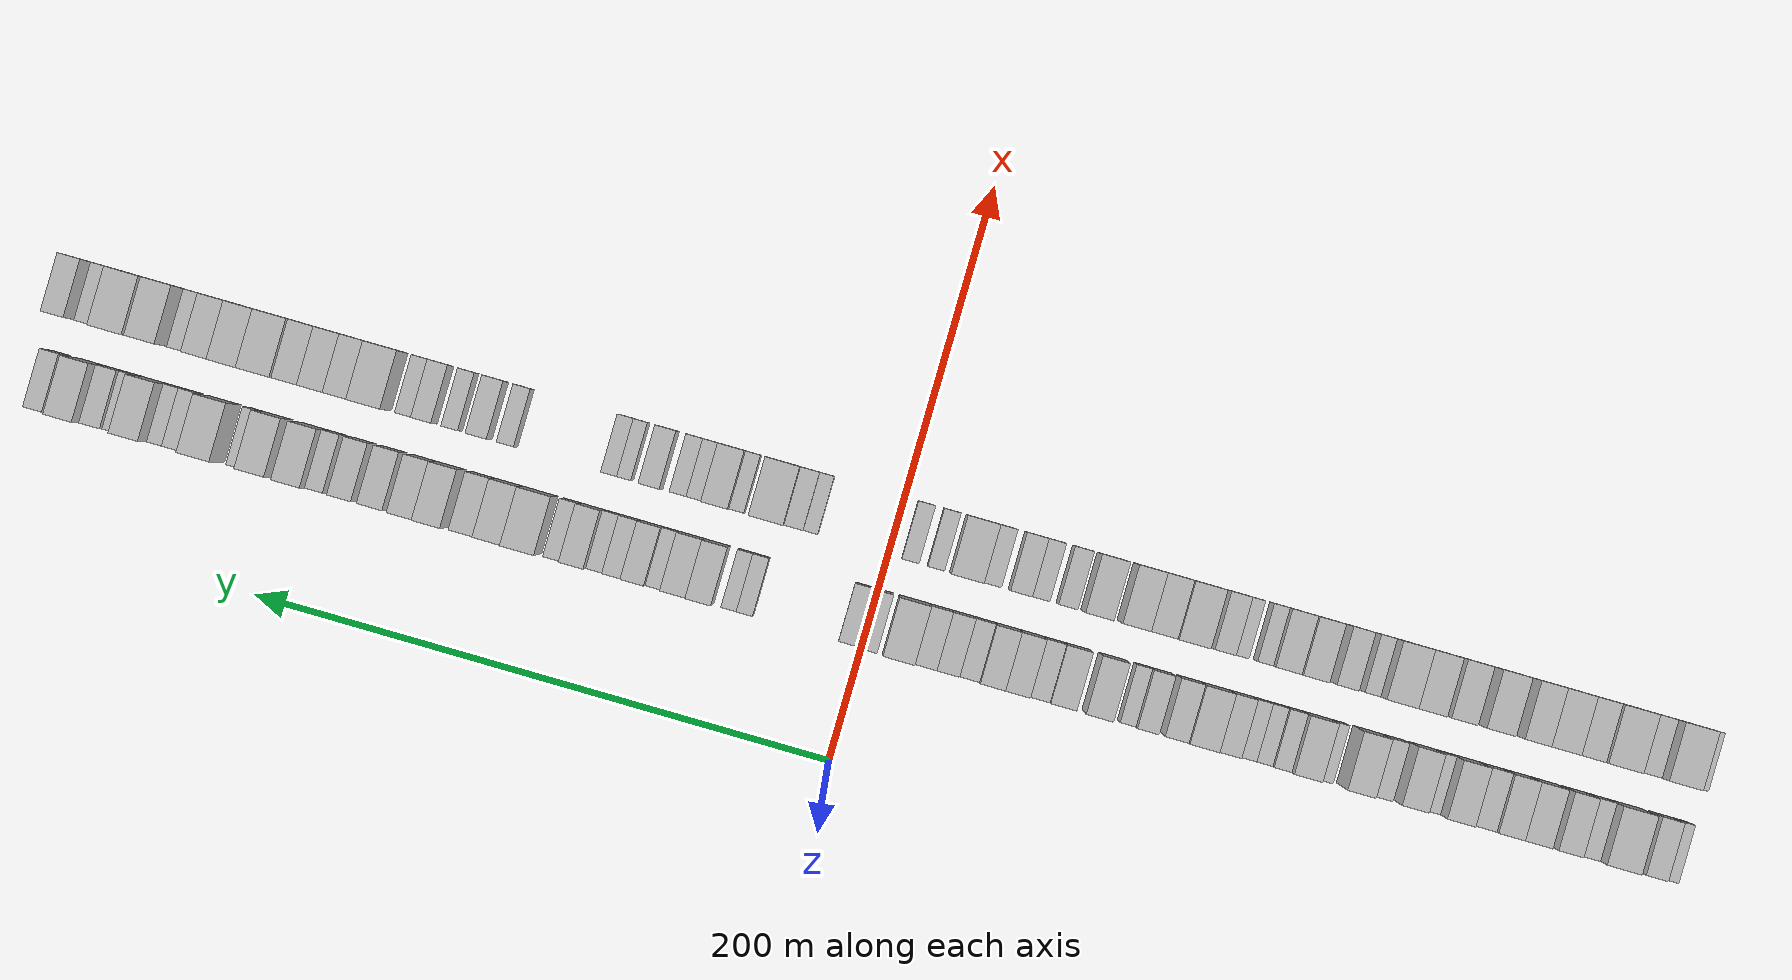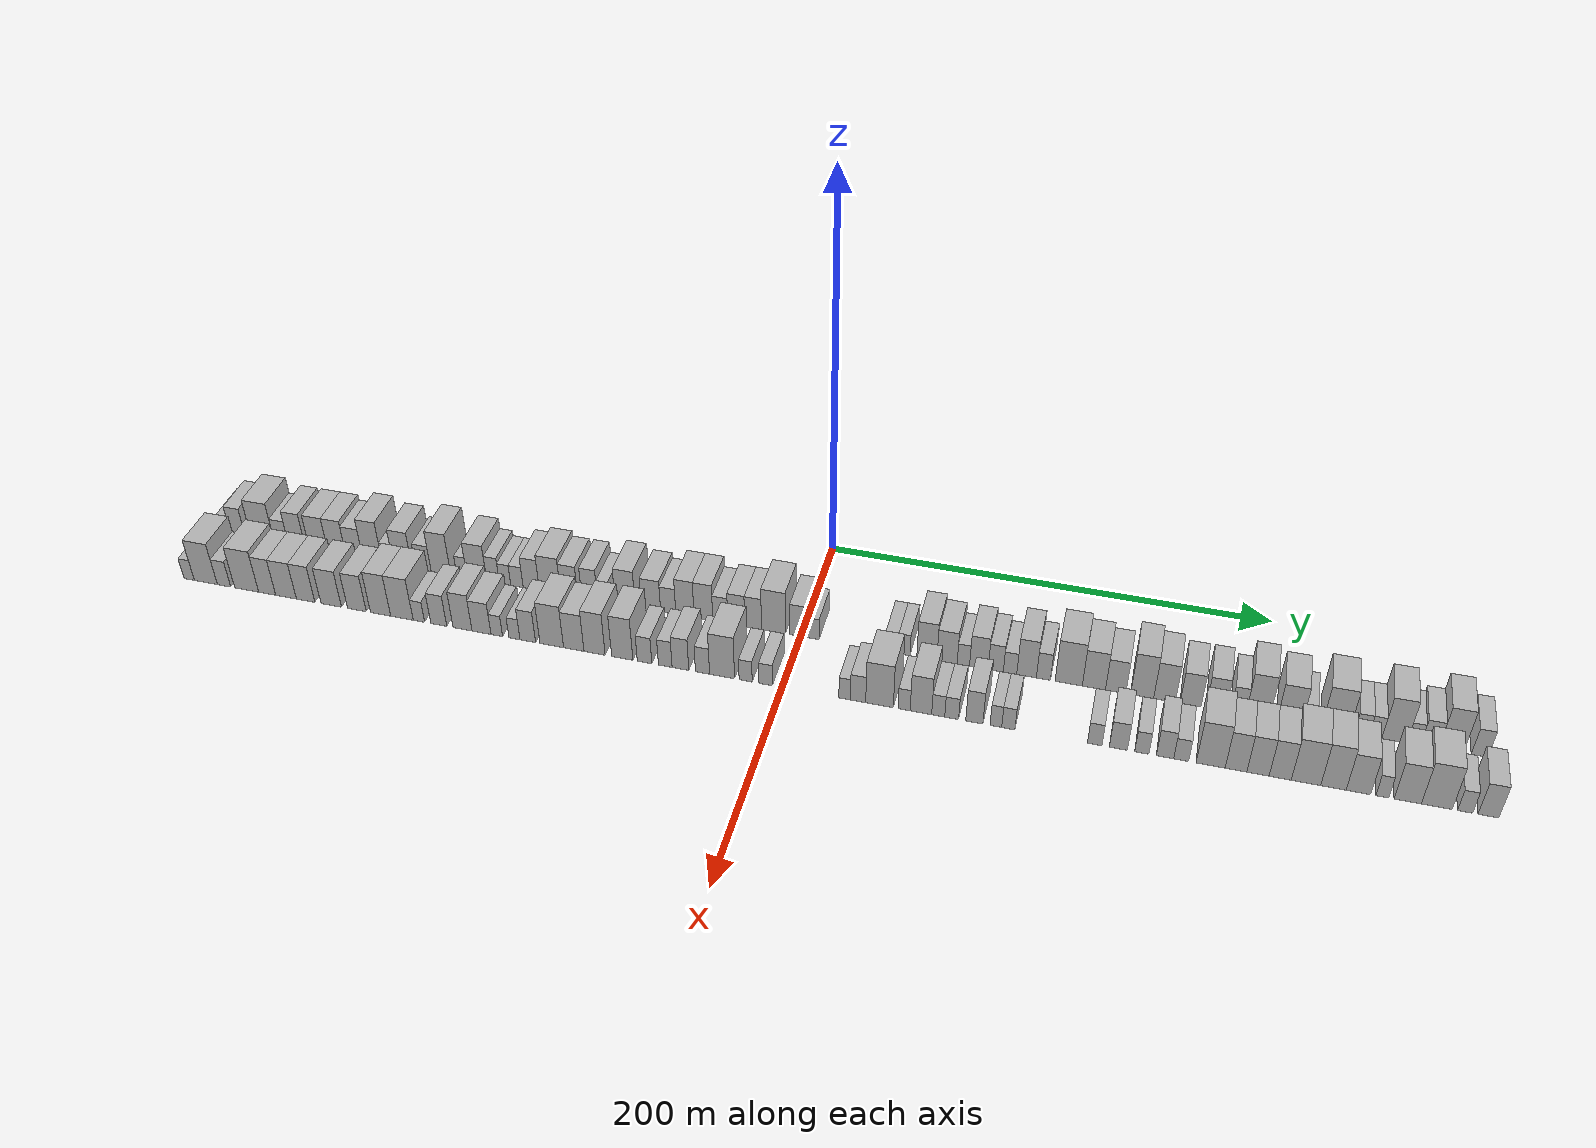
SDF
<sdf version="1.6">
 <world name="default">
  <scene>
   <sky><clouds><speed>12</speed></clouds></sky>
   <ambient>0.4 0.4 0.4 1</ambient>
   <background>0.7 0.7 0.7 1</background>
   <shadows>1</shadows>
  </scene>
  <gravity>0 0 -9.8066</gravity>
  <magnetic_field>6e-06 2.3e-05 -4.2e-05</magnetic_field>
  <physics default="0" name="default_physics" type="ode">
   <ode>
    <solver>
     <type>quick</type>
     <iters>10</iters>
     <sor>1.0</sor>
     <use_dynamic_moi_rescaling>0</use_dynamic_moi_rescaling>
    </solver>
    <constraints>
     <cfm>0</cfm>
     <erp>0.2</erp>
     <contact_max_correcting_vel>100</contact_max_correcting_vel>
     <contact_surface_layer>0.001</contact_surface_layer>
    </constraints>
   </ode>
   <max_step_size>0.004</max_step_size>
   <real_time_factor>1</real_time_factor>
   <real_time_update_rate>250</real_time_update_rate>
  </physics>
  <light name="sun" type="directional">
   <pose>0 0 10 0 0 0</pose>
   <diffuse>0.8 0.8 0.8 1</diffuse>
   <specular>0.2 0.2 0.2 1</specular>
   <attenuation>
    <range>1000</range>
    <constant>0.9</constant>
    <linear>0.01</linear>
    <quadratic>0.001</quadratic>
   </attenuation>
   <direction>-0.5 0.1 -0.9</direction>
  </light>
  <model name="building_1">
   <static>1</static>
   <pose>50.0000 -278.3909 0 0.000000 0.000000 0.000000</pose>
   <link name="link">
    <pose>0 0 6.00 0 0 0</pose>
    <collision name="collision"><geometry><box><size>20.0000 5.2182 12.0000</size></box></geometry></collision>
    <visual name="visual">
     <cast_shadows>0</cast_shadows>
     <geometry><box><size>20.0000 5.2182 12.0000</size></box></geometry>
     <material>
      <script>
       <uri>model://HANNAS_wall/materials/scripts</uri>
       <uri>model://HANNAS_wall/materials/textures</uri>
       <name>vrc/HANNAS_wall</name>
      </script>
     </material>
    </visual>
   </link>
  </model>
  <model name="building_2">
   <static>1</static>
   <pose>50.0000 -271.9759 0 0.000000 0.000000 0.000000</pose>
   <link name="link">
    <pose>0 0 9.00 0 0 0</pose>
    <collision name="collision"><geometry><box><size>20.0000 7.6117 18.0000</size></box></geometry></collision>
    <visual name="visual">
     <cast_shadows>0</cast_shadows>
     <geometry><box><size>20.0000 7.6117 18.0000</size></box></geometry>
     <material>
      <script>
       <uri>model://HANNAS_wall/materials/scripts</uri>
       <uri>model://HANNAS_wall/materials/textures</uri>
       <name>vrc/HANNAS_wall</name>
      </script>
     </material>
    </visual>
   </link>
  </model>
  <model name="building_3">
   <static>1</static>
   <pose>50.0000 -259.2273 0 0.000000 0.000000 0.000000</pose>
   <link name="link">
    <pose>0 0 12.00 0 0 0</pose>
    <collision name="collision"><geometry><box><size>20.0000 11.8855 24.0000</size></box></geometry></collision>
    <visual name="visual">
     <cast_shadows>0</cast_shadows>
     <geometry><box><size>20.0000 11.8855 24.0000</size></box></geometry>
     <material>
      <script>
       <uri>model://HANNAS_wall/materials/scripts</uri>
       <uri>model://HANNAS_wall/materials/textures</uri>
       <name>vrc/HANNAS_wall</name>
      </script>
     </material>
    </visual>
   </link>
  </model>
  <model name="building_4">
   <static>1</static>
   <pose>50.0000 -249.6853 0 0.000000 0.000000 0.000000</pose>
   <link name="link">
    <pose>0 0 7.50 0 0 0</pose>
    <collision name="collision"><geometry><box><size>20.0000 7.1986 15.0000</size></box></geometry></collision>
    <visual name="visual">
     <cast_shadows>0</cast_shadows>
     <geometry><box><size>20.0000 7.1986 15.0000</size></box></geometry>
     <material>
      <script>
       <uri>model://HANNAS_wall/materials/scripts</uri>
       <uri>model://HANNAS_wall/materials/textures</uri>
       <name>vrc/HANNAS_wall</name>
      </script>
     </material>
    </visual>
   </link>
  </model>
  <model name="building_5">
   <static>1</static>
   <pose>50.0000 -241.8243 0 0.000000 0.000000 0.000000</pose>
   <link name="link">
    <pose>0 0 10.50 0 0 0</pose>
    <collision name="collision"><geometry><box><size>20.0000 8.5234 21.0000</size></box></geometry></collision>
    <visual name="visual">
     <cast_shadows>0</cast_shadows>
     <geometry><box><size>20.0000 8.5234 21.0000</size></box></geometry>
     <material>
      <script>
       <uri>model://HANNAS_wall/materials/scripts</uri>
       <uri>model://HANNAS_wall/materials/textures</uri>
       <name>vrc/HANNAS_wall</name>
      </script>
     </material>
    </visual>
   </link>
  </model>
  <model name="building_6">
   <static>1</static>
   <pose>50.0000 -230.8683 0 0.000000 0.000000 0.000000</pose>
   <link name="link">
    <pose>0 0 10.50 0 0 0</pose>
    <collision name="collision"><geometry><box><size>20.0000 9.3886 21.0000</size></box></geometry></collision>
    <visual name="visual">
     <cast_shadows>0</cast_shadows>
     <geometry><box><size>20.0000 9.3886 21.0000</size></box></geometry>
     <material>
      <script>
       <uri>model://HANNAS_wall/materials/scripts</uri>
       <uri>model://HANNAS_wall/materials/textures</uri>
       <name>vrc/HANNAS_wall</name>
      </script>
     </material>
    </visual>
   </link>
  </model>
  <model name="building_7">
   <static>1</static>
   <pose>50.0000 -221.6379 0 0.000000 0.000000 0.000000</pose>
   <link name="link">
    <pose>0 0 10.50 0 0 0</pose>
    <collision name="collision"><geometry><box><size>20.0000 9.0723 21.0000</size></box></geometry></collision>
    <visual name="visual">
     <cast_shadows>0</cast_shadows>
     <geometry><box><size>20.0000 9.0723 21.0000</size></box></geometry>
     <material>
      <script>
       <uri>model://HANNAS_wall/materials/scripts</uri>
       <uri>model://HANNAS_wall/materials/textures</uri>
       <name>vrc/HANNAS_wall</name>
      </script>
     </material>
    </visual>
   </link>
  </model>
  <model name="building_8">
   <static>1</static>
   <pose>50.0000 -212.8523 0 0.000000 0.000000 0.000000</pose>
   <link name="link">
    <pose>0 0 9.00 0 0 0</pose>
    <collision name="collision"><geometry><box><size>20.0000 8.4987 18.0000</size></box></geometry></collision>
    <visual name="visual">
     <cast_shadows>0</cast_shadows>
     <geometry><box><size>20.0000 8.4987 18.0000</size></box></geometry>
     <material>
      <script>
       <uri>model://HANNAS_wall/materials/scripts</uri>
       <uri>model://HANNAS_wall/materials/textures</uri>
       <name>vrc/HANNAS_wall</name>
      </script>
     </material>
    </visual>
   </link>
  </model>
  <model name="building_9">
   <static>1</static>
   <pose>50.0000 -203.7990 0 0.000000 0.000000 0.000000</pose>
   <link name="link">
    <pose>0 0 12.00 0 0 0</pose>
    <collision name="collision"><geometry><box><size>20.0000 9.6079 24.0000</size></box></geometry></collision>
    <visual name="visual">
     <cast_shadows>0</cast_shadows>
     <geometry><box><size>20.0000 9.6079 24.0000</size></box></geometry>
     <material>
      <script>
       <uri>model://HANNAS_wall/materials/scripts</uri>
       <uri>model://HANNAS_wall/materials/textures</uri>
       <name>vrc/HANNAS_wall</name>
      </script>
     </material>
    </visual>
   </link>
  </model>
  <model name="building_10">
   <static>1</static>
   <pose>50.0000 -196.2178 0 0.000000 0.000000 0.000000</pose>
   <link name="link">
    <pose>0 0 6.00 0 0 0</pose>
    <collision name="collision"><geometry><box><size>20.0000 5.5546 12.0000</size></box></geometry></collision>
    <visual name="visual">
     <cast_shadows>0</cast_shadows>
     <geometry><box><size>20.0000 5.5546 12.0000</size></box></geometry>
     <material>
      <script>
       <uri>model://HANNAS_wall/materials/scripts</uri>
       <uri>model://HANNAS_wall/materials/textures</uri>
       <name>vrc/HANNAS_wall</name>
      </script>
     </material>
    </visual>
   </link>
  </model>
  <model name="building_11">
   <static>1</static>
   <pose>50.0000 -188.8204 0 0.000000 0.000000 0.000000</pose>
   <link name="link">
    <pose>0 0 10.50 0 0 0</pose>
    <collision name="collision"><geometry><box><size>20.0000 9.2402 21.0000</size></box></geometry></collision>
    <visual name="visual">
     <cast_shadows>0</cast_shadows>
     <geometry><box><size>20.0000 9.2402 21.0000</size></box></geometry>
     <material>
      <script>
       <uri>model://HANNAS_wall/materials/scripts</uri>
       <uri>model://HANNAS_wall/materials/textures</uri>
       <name>vrc/HANNAS_wall</name>
      </script>
     </material>
    </visual>
   </link>
  </model>
  <model name="building_12">
   <static>1</static>
   <pose>50.0000 -178.4922 0 0.000000 0.000000 0.000000</pose>
   <link name="link">
    <pose>0 0 7.50 0 0 0</pose>
    <collision name="collision"><geometry><box><size>20.0000 7.4162 15.0000</size></box></geometry></collision>
    <visual name="visual">
     <cast_shadows>0</cast_shadows>
     <geometry><box><size>20.0000 7.4162 15.0000</size></box></geometry>
     <material>
      <script>
       <uri>model://HANNAS_wall/materials/scripts</uri>
       <uri>model://HANNAS_wall/materials/textures</uri>
       <name>vrc/HANNAS_wall</name>
      </script>
     </material>
    </visual>
   </link>
  </model>
  <model name="building_13">
   <static>1</static>
   <pose>50.0000 -169.9375 0 0.000000 0.000000 0.000000</pose>
   <link name="link">
    <pose>0 0 12.00 0 0 0</pose>
    <collision name="collision"><geometry><box><size>20.0000 9.6934 24.0000</size></box></geometry></collision>
    <visual name="visual">
     <cast_shadows>0</cast_shadows>
     <geometry><box><size>20.0000 9.6934 24.0000</size></box></geometry>
     <material>
      <script>
       <uri>model://HANNAS_wall/materials/scripts</uri>
       <uri>model://HANNAS_wall/materials/textures</uri>
       <name>vrc/HANNAS_wall</name>
      </script>
     </material>
    </visual>
   </link>
  </model>
  <model name="building_14">
   <static>1</static>
   <pose>50.0000 -159.5936 0 0.000000 0.000000 0.000000</pose>
   <link name="link">
    <pose>0 0 6.00 0 0 0</pose>
    <collision name="collision"><geometry><box><size>20.0000 4.9944 12.0000</size></box></geometry></collision>
    <visual name="visual">
     <cast_shadows>0</cast_shadows>
     <geometry><box><size>20.0000 4.9944 12.0000</size></box></geometry>
     <material>
      <script>
       <uri>model://HANNAS_wall/materials/scripts</uri>
       <uri>model://HANNAS_wall/materials/textures</uri>
       <name>vrc/HANNAS_wall</name>
      </script>
     </material>
    </visual>
   </link>
  </model>
  <model name="building_15">
   <static>1</static>
   <pose>50.0000 -152.2584 0 0.000000 0.000000 0.000000</pose>
   <link name="link">
    <pose>0 0 10.50 0 0 0</pose>
    <collision name="collision"><geometry><box><size>20.0000 9.6758 21.0000</size></box></geometry></collision>
    <visual name="visual">
     <cast_shadows>0</cast_shadows>
     <geometry><box><size>20.0000 9.6758 21.0000</size></box></geometry>
     <material>
      <script>
       <uri>model://HANNAS_wall/materials/scripts</uri>
       <uri>model://HANNAS_wall/materials/textures</uri>
       <name>vrc/HANNAS_wall</name>
      </script>
     </material>
    </visual>
   </link>
  </model>
  <model name="building_16">
   <static>1</static>
   <pose>50.0000 -144.3793 0 0.000000 0.000000 0.000000</pose>
   <link name="link">
    <pose>0 0 7.50 0 0 0</pose>
    <collision name="collision"><geometry><box><size>20.0000 6.0824 15.0000</size></box></geometry></collision>
    <visual name="visual">
     <cast_shadows>0</cast_shadows>
     <geometry><box><size>20.0000 6.0824 15.0000</size></box></geometry>
     <material>
      <script>
       <uri>model://HANNAS_wall/materials/scripts</uri>
       <uri>model://HANNAS_wall/materials/textures</uri>
       <name>vrc/HANNAS_wall</name>
      </script>
     </material>
    </visual>
   </link>
  </model>
  <model name="building_17">
   <static>1</static>
   <pose>50.0000 -138.5889 0 0.000000 0.000000 0.000000</pose>
   <link name="link">
    <pose>0 0 6.00 0 0 0</pose>
    <collision name="collision"><geometry><box><size>20.0000 5.4985 12.0000</size></box></geometry></collision>
    <visual name="visual">
     <cast_shadows>0</cast_shadows>
     <geometry><box><size>20.0000 5.4985 12.0000</size></box></geometry>
     <material>
      <script>
       <uri>model://HANNAS_wall/materials/scripts</uri>
       <uri>model://HANNAS_wall/materials/textures</uri>
       <name>vrc/HANNAS_wall</name>
      </script>
     </material>
    </visual>
   </link>
  </model>
  <model name="building_18">
   <static>1</static>
   <pose>50.0000 -132.8439 0 0.000000 0.000000 0.000000</pose>
   <link name="link">
    <pose>0 0 6.00 0 0 0</pose>
    <collision name="collision"><geometry><box><size>20.0000 5.9916 12.0000</size></box></geometry></collision>
    <visual name="visual">
     <cast_shadows>0</cast_shadows>
     <geometry><box><size>20.0000 5.9916 12.0000</size></box></geometry>
     <material>
      <script>
       <uri>model://HANNAS_wall/materials/scripts</uri>
       <uri>model://HANNAS_wall/materials/textures</uri>
       <name>vrc/HANNAS_wall</name>
      </script>
     </material>
    </visual>
   </link>
  </model>
  <model name="building_19">
   <static>1</static>
   <pose>50.0000 -125.9320 0 0.000000 0.000000 0.000000</pose>
   <link name="link">
    <pose>0 0 9.00 0 0 0</pose>
    <collision name="collision"><geometry><box><size>20.0000 7.8322 18.0000</size></box></geometry></collision>
    <visual name="visual">
     <cast_shadows>0</cast_shadows>
     <geometry><box><size>20.0000 7.8322 18.0000</size></box></geometry>
     <material>
      <script>
       <uri>model://HANNAS_wall/materials/scripts</uri>
       <uri>model://HANNAS_wall/materials/textures</uri>
       <name>vrc/HANNAS_wall</name>
      </script>
     </material>
    </visual>
   </link>
  </model>
  <model name="building_20">
   <static>1</static>
   <pose>50.0000 -116.9215 0 0.000000 0.000000 0.000000</pose>
   <link name="link">
    <pose>0 0 10.50 0 0 0</pose>
    <collision name="collision"><geometry><box><size>20.0000 10.1887 21.0000</size></box></geometry></collision>
    <visual name="visual">
     <cast_shadows>0</cast_shadows>
     <geometry><box><size>20.0000 10.1887 21.0000</size></box></geometry>
     <material>
      <script>
       <uri>model://HANNAS_wall/materials/scripts</uri>
       <uri>model://HANNAS_wall/materials/textures</uri>
       <name>vrc/HANNAS_wall</name>
      </script>
     </material>
    </visual>
   </link>
  </model>
  <model name="building_21">
   <static>1</static>
   <pose>50.0000 -107.7564 0 0.000000 0.000000 0.000000</pose>
   <link name="link">
    <pose>0 0 9.00 0 0 0</pose>
    <collision name="collision"><geometry><box><size>20.0000 8.1417 18.0000</size></box></geometry></collision>
    <visual name="visual">
     <cast_shadows>0</cast_shadows>
     <geometry><box><size>20.0000 8.1417 18.0000</size></box></geometry>
     <material>
      <script>
       <uri>model://HANNAS_wall/materials/scripts</uri>
       <uri>model://HANNAS_wall/materials/textures</uri>
       <name>vrc/HANNAS_wall</name>
      </script>
     </material>
    </visual>
   </link>
  </model>
  <model name="building_22">
   <static>1</static>
   <pose>50.0000 -97.9635 0 0.000000 0.000000 0.000000</pose>
   <link name="link">
    <pose>0 0 9.00 0 0 0</pose>
    <collision name="collision"><geometry><box><size>20.0000 7.4440 18.0000</size></box></geometry></collision>
    <visual name="visual">
     <cast_shadows>0</cast_shadows>
     <geometry><box><size>20.0000 7.4440 18.0000</size></box></geometry>
     <material>
      <script>
       <uri>model://HANNAS_wall/materials/scripts</uri>
       <uri>model://HANNAS_wall/materials/textures</uri>
       <name>vrc/HANNAS_wall</name>
      </script>
     </material>
    </visual>
   </link>
  </model>
  <model name="building_23">
   <static>1</static>
   <pose>50.0000 -91.5334 0 0.000000 0.000000 0.000000</pose>
   <link name="link">
    <pose>0 0 6.00 0 0 0</pose>
    <collision name="collision"><geometry><box><size>20.0000 5.4163 12.0000</size></box></geometry></collision>
    <visual name="visual">
     <cast_shadows>0</cast_shadows>
     <geometry><box><size>20.0000 5.4163 12.0000</size></box></geometry>
     <material>
      <script>
       <uri>model://HANNAS_wall/materials/scripts</uri>
       <uri>model://HANNAS_wall/materials/textures</uri>
       <name>vrc/HANNAS_wall</name>
      </script>
     </material>
    </visual>
   </link>
  </model>
  <model name="building_24">
   <static>1</static>
   <pose>50.0000 -81.1538 0 0.000000 0.000000 0.000000</pose>
   <link name="link">
    <pose>0 0 10.50 0 0 0</pose>
    <collision name="collision"><geometry><box><size>20.0000 9.3428 21.0000</size></box></geometry></collision>
    <visual name="visual">
     <cast_shadows>0</cast_shadows>
     <geometry><box><size>20.0000 9.3428 21.0000</size></box></geometry>
     <material>
      <script>
       <uri>model://HANNAS_wall/materials/scripts</uri>
       <uri>model://HANNAS_wall/materials/textures</uri>
       <name>vrc/HANNAS_wall</name>
      </script>
     </material>
    </visual>
   </link>
  </model>
  <model name="building_25">
   <static>1</static>
   <pose>50.0000 -69.0168 0 0.000000 0.000000 0.000000</pose>
   <link name="link">
    <pose>0 0 9.00 0 0 0</pose>
    <collision name="collision"><geometry><box><size>20.0000 8.9312 18.0000</size></box></geometry></collision>
    <visual name="visual">
     <cast_shadows>0</cast_shadows>
     <geometry><box><size>20.0000 8.9312 18.0000</size></box></geometry>
     <material>
      <script>
       <uri>model://HANNAS_wall/materials/scripts</uri>
       <uri>model://HANNAS_wall/materials/textures</uri>
       <name>vrc/HANNAS_wall</name>
      </script>
     </material>
    </visual>
   </link>
  </model>
  <model name="building_26">
   <static>1</static>
   <pose>50.0000 -61.0077 0 0.000000 0.000000 0.000000</pose>
   <link name="link">
    <pose>0 0 7.50 0 0 0</pose>
    <collision name="collision"><geometry><box><size>20.0000 7.0871 15.0000</size></box></geometry></collision>
    <visual name="visual">
     <cast_shadows>0</cast_shadows>
     <geometry><box><size>20.0000 7.0871 15.0000</size></box></geometry>
     <material>
      <script>
       <uri>model://HANNAS_wall/materials/scripts</uri>
       <uri>model://HANNAS_wall/materials/textures</uri>
       <name>vrc/HANNAS_wall</name>
      </script>
     </material>
    </visual>
   </link>
  </model>
  <model name="building_27">
   <static>1</static>
   <pose>50.0000 -53.2156 0 0.000000 0.000000 0.000000</pose>
   <link name="link">
    <pose>0 0 10.50 0 0 0</pose>
    <collision name="collision"><geometry><box><size>20.0000 8.4971 21.0000</size></box></geometry></collision>
    <visual name="visual">
     <cast_shadows>0</cast_shadows>
     <geometry><box><size>20.0000 8.4971 21.0000</size></box></geometry>
     <material>
      <script>
       <uri>model://HANNAS_wall/materials/scripts</uri>
       <uri>model://HANNAS_wall/materials/textures</uri>
       <name>vrc/HANNAS_wall</name>
      </script>
     </material>
    </visual>
   </link>
  </model>
  <model name="building_28">
   <static>1</static>
   <pose>50.0000 -44.6585 0 0.000000 0.000000 0.000000</pose>
   <link name="link">
    <pose>0 0 10.50 0 0 0</pose>
    <collision name="collision"><geometry><box><size>20.0000 8.6171 21.0000</size></box></geometry></collision>
    <visual name="visual">
     <cast_shadows>0</cast_shadows>
     <geometry><box><size>20.0000 8.6171 21.0000</size></box></geometry>
     <material>
      <script>
       <uri>model://HANNAS_wall/materials/scripts</uri>
       <uri>model://HANNAS_wall/materials/textures</uri>
       <name>vrc/HANNAS_wall</name>
      </script>
     </material>
    </visual>
   </link>
  </model>
  <model name="building_29">
   <static>1</static>
   <pose>50.0000 -36.8754 0 0.000000 0.000000 0.000000</pose>
   <link name="link">
    <pose>0 0 7.50 0 0 0</pose>
    <collision name="collision"><geometry><box><size>20.0000 6.9492 15.0000</size></box></geometry></collision>
    <visual name="visual">
     <cast_shadows>0</cast_shadows>
     <geometry><box><size>20.0000 6.9492 15.0000</size></box></geometry>
     <material>
      <script>
       <uri>model://HANNAS_wall/materials/scripts</uri>
       <uri>model://HANNAS_wall/materials/textures</uri>
       <name>vrc/HANNAS_wall</name>
      </script>
     </material>
    </visual>
   </link>
  </model>
  <model name="building_30">
   <static>1</static>
   <pose>50.0000 -29.5165 0 0.000000 0.000000 0.000000</pose>
   <link name="link">
    <pose>0 0 9.00 0 0 0</pose>
    <collision name="collision"><geometry><box><size>20.0000 7.7685 18.0000</size></box></geometry></collision>
    <visual name="visual">
     <cast_shadows>0</cast_shadows>
     <geometry><box><size>20.0000 7.7685 18.0000</size></box></geometry>
     <material>
      <script>
       <uri>model://HANNAS_wall/materials/scripts</uri>
       <uri>model://HANNAS_wall/materials/textures</uri>
       <name>vrc/HANNAS_wall</name>
      </script>
     </material>
    </visual>
   </link>
  </model>
  <model name="building_31">
   <static>1</static>
   <pose>50.0000 -21.8159 0 0.000000 0.000000 0.000000</pose>
   <link name="link">
    <pose>0 0 9.00 0 0 0</pose>
    <collision name="collision"><geometry><box><size>20.0000 7.6327 18.0000</size></box></geometry></collision>
    <visual name="visual">
     <cast_shadows>0</cast_shadows>
     <geometry><box><size>20.0000 7.6327 18.0000</size></box></geometry>
     <material>
      <script>
       <uri>model://HANNAS_wall/materials/scripts</uri>
       <uri>model://HANNAS_wall/materials/textures</uri>
       <name>vrc/HANNAS_wall</name>
      </script>
     </material>
    </visual>
   </link>
  </model>
  <model name="building_32">
   <static>1</static>
   <pose>50.0000 -12.5680 0 0.000000 0.000000 0.000000</pose>
   <link name="link">
    <pose>0 0 12.00 0 0 0</pose>
    <collision name="collision"><geometry><box><size>20.0000 10.8629 24.0000</size></box></geometry></collision>
    <visual name="visual">
     <cast_shadows>0</cast_shadows>
     <geometry><box><size>20.0000 10.8629 24.0000</size></box></geometry>
     <material>
      <script>
       <uri>model://HANNAS_wall/materials/scripts</uri>
       <uri>model://HANNAS_wall/materials/textures</uri>
       <name>vrc/HANNAS_wall</name>
      </script>
     </material>
    </visual>
   </link>
  </model>
  <model name="building_33">
   <static>1</static>
   <pose>50.0000 -1.3900 0 0.000000 0.000000 0.000000</pose>
   <link name="link">
    <pose>0 0 9.00 0 0 0</pose>
    <collision name="collision"><geometry><box><size>20.0000 7.4931 18.0000</size></box></geometry></collision>
    <visual name="visual">
     <cast_shadows>0</cast_shadows>
     <geometry><box><size>20.0000 7.4931 18.0000</size></box></geometry>
     <material>
      <script>
       <uri>model://HANNAS_wall/materials/scripts</uri>
       <uri>model://HANNAS_wall/materials/textures</uri>
       <name>vrc/HANNAS_wall</name>
      </script>
     </material>
    </visual>
   </link>
  </model>
  <model name="building_34">
   <static>1</static>
   <pose>50.0000 5.2241 0 0.000000 0.000000 0.000000</pose>
   <link name="link">
    <pose>0 0 6.00 0 0 0</pose>
    <collision name="collision"><geometry><box><size>20.0000 5.7352 12.0000</size></box></geometry></collision>
    <visual name="visual">
     <cast_shadows>0</cast_shadows>
     <geometry><box><size>20.0000 5.7352 12.0000</size></box></geometry>
     <material>
      <script>
       <uri>model://HANNAS_wall/materials/scripts</uri>
       <uri>model://HANNAS_wall/materials/textures</uri>
       <name>vrc/HANNAS_wall</name>
      </script>
     </material>
    </visual>
   </link>
  </model>
  <model name="building_35">
   <static>1</static>
   <pose>50.0000 40.5400 0 0.000000 0.000000 0.000000</pose>
   <link name="link">
    <pose>0 0 6.00 0 0 0</pose>
    <collision name="collision"><geometry><box><size>20.0000 5.6322 12.0000</size></box></geometry></collision>
    <visual name="visual">
     <cast_shadows>0</cast_shadows>
     <geometry><box><size>20.0000 5.6322 12.0000</size></box></geometry>
     <material>
      <script>
       <uri>model://HANNAS_wall/materials/scripts</uri>
       <uri>model://HANNAS_wall/materials/textures</uri>
       <name>vrc/HANNAS_wall</name>
      </script>
     </material>
    </visual>
   </link>
  </model>
  <model name="building_36">
   <static>1</static>
   <pose>50.0000 45.9921 0 0.000000 0.000000 0.000000</pose>
   <link name="link">
    <pose>0 0 6.00 0 0 0</pose>
    <collision name="collision"><geometry><box><size>20.0000 5.2721 12.0000</size></box></geometry></collision>
    <visual name="visual">
     <cast_shadows>0</cast_shadows>
     <geometry><box><size>20.0000 5.2721 12.0000</size></box></geometry>
     <material>
      <script>
       <uri>model://HANNAS_wall/materials/scripts</uri>
       <uri>model://HANNAS_wall/materials/textures</uri>
       <name>vrc/HANNAS_wall</name>
      </script>
     </material>
    </visual>
   </link>
  </model>
  <model name="building_37">
   <static>1</static>
   <pose>50.0000 56.0227 0 0.000000 0.000000 0.000000</pose>
   <link name="link">
    <pose>0 0 10.50 0 0 0</pose>
    <collision name="collision"><geometry><box><size>20.0000 8.7891 21.0000</size></box></geometry></collision>
    <visual name="visual">
     <cast_shadows>0</cast_shadows>
     <geometry><box><size>20.0000 8.7891 21.0000</size></box></geometry>
     <material>
      <script>
       <uri>model://HANNAS_wall/materials/scripts</uri>
       <uri>model://HANNAS_wall/materials/textures</uri>
       <name>vrc/HANNAS_wall</name>
      </script>
     </material>
    </visual>
   </link>
  </model>
  <model name="building_38">
   <static>1</static>
   <pose>50.0000 64.8491 0 0.000000 0.000000 0.000000</pose>
   <link name="link">
    <pose>0 0 9.00 0 0 0</pose>
    <collision name="collision"><geometry><box><size>20.0000 8.8636 18.0000</size></box></geometry></collision>
    <visual name="visual">
     <cast_shadows>0</cast_shadows>
     <geometry><box><size>20.0000 8.8636 18.0000</size></box></geometry>
     <material>
      <script>
       <uri>model://HANNAS_wall/materials/scripts</uri>
       <uri>model://HANNAS_wall/materials/textures</uri>
       <name>vrc/HANNAS_wall</name>
      </script>
     </material>
    </visual>
   </link>
  </model>
  <model name="building_39">
   <static>1</static>
   <pose>50.0000 71.9994 0 0.000000 0.000000 0.000000</pose>
   <link name="link">
    <pose>0 0 6.00 0 0 0</pose>
    <collision name="collision"><geometry><box><size>20.0000 5.4370 12.0000</size></box></geometry></collision>
    <visual name="visual">
     <cast_shadows>0</cast_shadows>
     <geometry><box><size>20.0000 5.4370 12.0000</size></box></geometry>
     <material>
      <script>
       <uri>model://HANNAS_wall/materials/scripts</uri>
       <uri>model://HANNAS_wall/materials/textures</uri>
       <name>vrc/HANNAS_wall</name>
      </script>
     </material>
    </visual>
   </link>
  </model>
  <model name="building_40">
   <static>1</static>
   <pose>50.0000 78.7575 0 0.000000 0.000000 0.000000</pose>
   <link name="link">
    <pose>0 0 9.00 0 0 0</pose>
    <collision name="collision"><geometry><box><size>20.0000 8.0791 18.0000</size></box></geometry></collision>
    <visual name="visual">
     <cast_shadows>0</cast_shadows>
     <geometry><box><size>20.0000 8.0791 18.0000</size></box></geometry>
     <material>
      <script>
       <uri>model://HANNAS_wall/materials/scripts</uri>
       <uri>model://HANNAS_wall/materials/textures</uri>
       <name>vrc/HANNAS_wall</name>
      </script>
     </material>
    </visual>
   </link>
  </model>
  <model name="building_41">
   <static>1</static>
   <pose>50.0000 86.0763 0 0.000000 0.000000 0.000000</pose>
   <link name="link">
    <pose>0 0 7.50 0 0 0</pose>
    <collision name="collision"><geometry><box><size>20.0000 6.5585 15.0000</size></box></geometry></collision>
    <visual name="visual">
     <cast_shadows>0</cast_shadows>
     <geometry><box><size>20.0000 6.5585 15.0000</size></box></geometry>
     <material>
      <script>
       <uri>model://HANNAS_wall/materials/scripts</uri>
       <uri>model://HANNAS_wall/materials/textures</uri>
       <name>vrc/HANNAS_wall</name>
      </script>
     </material>
    </visual>
   </link>
  </model>
  <model name="building_42">
   <static>1</static>
   <pose>50.0000 92.2538 0 0.000000 0.000000 0.000000</pose>
   <link name="link">
    <pose>0 0 6.00 0 0 0</pose>
    <collision name="collision"><geometry><box><size>20.0000 5.7967 12.0000</size></box></geometry></collision>
    <visual name="visual">
     <cast_shadows>0</cast_shadows>
     <geometry><box><size>20.0000 5.7967 12.0000</size></box></geometry>
     <material>
      <script>
       <uri>model://HANNAS_wall/materials/scripts</uri>
       <uri>model://HANNAS_wall/materials/textures</uri>
       <name>vrc/HANNAS_wall</name>
      </script>
     </material>
    </visual>
   </link>
  </model>
  <model name="building_43">
   <static>1</static>
   <pose>50.0000 99.3555 0 0.000000 0.000000 0.000000</pose>
   <link name="link">
    <pose>0 0 10.50 0 0 0</pose>
    <collision name="collision"><geometry><box><size>20.0000 8.4067 21.0000</size></box></geometry></collision>
    <visual name="visual">
     <cast_shadows>0</cast_shadows>
     <geometry><box><size>20.0000 8.4067 21.0000</size></box></geometry>
     <material>
      <script>
       <uri>model://HANNAS_wall/materials/scripts</uri>
       <uri>model://HANNAS_wall/materials/textures</uri>
       <name>vrc/HANNAS_wall</name>
      </script>
     </material>
    </visual>
   </link>
  </model>
  <model name="building_44">
   <static>1</static>
   <pose>50.0000 106.5774 0 0.000000 0.000000 0.000000</pose>
   <link name="link">
    <pose>0 0 7.50 0 0 0</pose>
    <collision name="collision"><geometry><box><size>20.0000 6.0372 15.0000</size></box></geometry></collision>
    <visual name="visual">
     <cast_shadows>0</cast_shadows>
     <geometry><box><size>20.0000 6.0372 15.0000</size></box></geometry>
     <material>
      <script>
       <uri>model://HANNAS_wall/materials/scripts</uri>
       <uri>model://HANNAS_wall/materials/textures</uri>
       <name>vrc/HANNAS_wall</name>
      </script>
     </material>
    </visual>
   </link>
  </model>
  <model name="building_45">
   <static>1</static>
   <pose>50.0000 117.4008 0 0.000000 0.000000 0.000000</pose>
   <link name="link">
    <pose>0 0 12.00 0 0 0</pose>
    <collision name="collision"><geometry><box><size>20.0000 11.6096 24.0000</size></box></geometry></collision>
    <visual name="visual">
     <cast_shadows>0</cast_shadows>
     <geometry><box><size>20.0000 11.6096 24.0000</size></box></geometry>
     <material>
      <script>
       <uri>model://HANNAS_wall/materials/scripts</uri>
       <uri>model://HANNAS_wall/materials/textures</uri>
       <name>vrc/HANNAS_wall</name>
      </script>
     </material>
    </visual>
   </link>
  </model>
  <model name="building_46">
   <static>1</static>
   <pose>50.0000 128.1020 0 0.000000 0.000000 0.000000</pose>
   <link name="link">
    <pose>0 0 10.50 0 0 0</pose>
    <collision name="collision"><geometry><box><size>20.0000 9.7929 21.0000</size></box></geometry></collision>
    <visual name="visual">
     <cast_shadows>0</cast_shadows>
     <geometry><box><size>20.0000 9.7929 21.0000</size></box></geometry>
     <material>
      <script>
       <uri>model://HANNAS_wall/materials/scripts</uri>
       <uri>model://HANNAS_wall/materials/textures</uri>
       <name>vrc/HANNAS_wall</name>
      </script>
     </material>
    </visual>
   </link>
  </model>
  <model name="building_47">
   <static>1</static>
   <pose>50.0000 137.2708 0 0.000000 0.000000 0.000000</pose>
   <link name="link">
    <pose>0 0 9.00 0 0 0</pose>
    <collision name="collision"><geometry><box><size>20.0000 8.5446 18.0000</size></box></geometry></collision>
    <visual name="visual">
     <cast_shadows>0</cast_shadows>
     <geometry><box><size>20.0000 8.5446 18.0000</size></box></geometry>
     <material>
      <script>
       <uri>model://HANNAS_wall/materials/scripts</uri>
       <uri>model://HANNAS_wall/materials/textures</uri>
       <name>vrc/HANNAS_wall</name>
      </script>
     </material>
    </visual>
   </link>
  </model>
  <model name="building_48">
   <static>1</static>
   <pose>50.0000 148.3784 0 0.000000 0.000000 0.000000</pose>
   <link name="link">
    <pose>0 0 12.00 0 0 0</pose>
    <collision name="collision"><geometry><box><size>20.0000 9.6707 24.0000</size></box></geometry></collision>
    <visual name="visual">
     <cast_shadows>0</cast_shadows>
     <geometry><box><size>20.0000 9.6707 24.0000</size></box></geometry>
     <material>
      <script>
       <uri>model://HANNAS_wall/materials/scripts</uri>
       <uri>model://HANNAS_wall/materials/textures</uri>
       <name>vrc/HANNAS_wall</name>
      </script>
     </material>
    </visual>
   </link>
  </model>
  <model name="building_49">
   <static>1</static>
   <pose>50.0000 157.7045 0 0.000000 0.000000 0.000000</pose>
   <link name="link">
    <pose>0 0 10.50 0 0 0</pose>
    <collision name="collision"><geometry><box><size>20.0000 8.9815 21.0000</size></box></geometry></collision>
    <visual name="visual">
     <cast_shadows>0</cast_shadows>
     <geometry><box><size>20.0000 8.9815 21.0000</size></box></geometry>
     <material>
      <script>
       <uri>model://HANNAS_wall/materials/scripts</uri>
       <uri>model://HANNAS_wall/materials/textures</uri>
       <name>vrc/HANNAS_wall</name>
      </script>
     </material>
    </visual>
   </link>
  </model>
  <model name="building_50">
   <static>1</static>
   <pose>50.0000 168.5529 0 0.000000 0.000000 0.000000</pose>
   <link name="link">
    <pose>0 0 9.00 0 0 0</pose>
    <collision name="collision"><geometry><box><size>20.0000 8.7153 18.0000</size></box></geometry></collision>
    <visual name="visual">
     <cast_shadows>0</cast_shadows>
     <geometry><box><size>20.0000 8.7153 18.0000</size></box></geometry>
     <material>
      <script>
       <uri>model://HANNAS_wall/materials/scripts</uri>
       <uri>model://HANNAS_wall/materials/textures</uri>
       <name>vrc/HANNAS_wall</name>
      </script>
     </material>
    </visual>
   </link>
  </model>
  <model name="building_51">
   <static>1</static>
   <pose>50.0000 179.0079 0 0.000000 0.000000 0.000000</pose>
   <link name="link">
    <pose>0 0 9.00 0 0 0</pose>
    <collision name="collision"><geometry><box><size>20.0000 8.1946 18.0000</size></box></geometry></collision>
    <visual name="visual">
     <cast_shadows>0</cast_shadows>
     <geometry><box><size>20.0000 8.1946 18.0000</size></box></geometry>
     <material>
      <script>
       <uri>model://HANNAS_wall/materials/scripts</uri>
       <uri>model://HANNAS_wall/materials/textures</uri>
       <name>vrc/HANNAS_wall</name>
      </script>
     </material>
    </visual>
   </link>
  </model>
  <model name="building_52">
   <static>1</static>
   <pose>50.0000 188.1663 0 0.000000 0.000000 0.000000</pose>
   <link name="link">
    <pose>0 0 7.50 0 0 0</pose>
    <collision name="collision"><geometry><box><size>20.0000 6.1223 15.0000</size></box></geometry></collision>
    <visual name="visual">
     <cast_shadows>0</cast_shadows>
     <geometry><box><size>20.0000 6.1223 15.0000</size></box></geometry>
     <material>
      <script>
       <uri>model://HANNAS_wall/materials/scripts</uri>
       <uri>model://HANNAS_wall/materials/textures</uri>
       <name>vrc/HANNAS_wall</name>
      </script>
     </material>
    </visual>
   </link>
  </model>
  <model name="building_53">
   <static>1</static>
   <pose>50.0000 196.1051 0 0.000000 0.000000 0.000000</pose>
   <link name="link">
    <pose>0 0 12.00 0 0 0</pose>
    <collision name="collision"><geometry><box><size>20.0000 9.7553 24.0000</size></box></geometry></collision>
    <visual name="visual">
     <cast_shadows>0</cast_shadows>
     <geometry><box><size>20.0000 9.7553 24.0000</size></box></geometry>
     <material>
      <script>
       <uri>model://HANNAS_wall/materials/scripts</uri>
       <uri>model://HANNAS_wall/materials/textures</uri>
       <name>vrc/HANNAS_wall</name>
      </script>
     </material>
    </visual>
   </link>
  </model>
  <model name="building_54">
   <static>1</static>
   <pose>50.0000 209.0655 0 0.000000 0.000000 0.000000</pose>
   <link name="link">
    <pose>0 0 10.50 0 0 0</pose>
    <collision name="collision"><geometry><box><size>20.0000 10.1656 21.0000</size></box></geometry></collision>
    <visual name="visual">
     <cast_shadows>0</cast_shadows>
     <geometry><box><size>20.0000 10.1656 21.0000</size></box></geometry>
     <material>
      <script>
       <uri>model://HANNAS_wall/materials/scripts</uri>
       <uri>model://HANNAS_wall/materials/textures</uri>
       <name>vrc/HANNAS_wall</name>
      </script>
     </material>
    </visual>
   </link>
  </model>
  <model name="building_55">
   <static>1</static>
   <pose>50.0000 216.5581 0 0.000000 0.000000 0.000000</pose>
   <link name="link">
    <pose>0 0 6.00 0 0 0</pose>
    <collision name="collision"><geometry><box><size>20.0000 4.8195 12.0000</size></box></geometry></collision>
    <visual name="visual">
     <cast_shadows>0</cast_shadows>
     <geometry><box><size>20.0000 4.8195 12.0000</size></box></geometry>
     <material>
      <script>
       <uri>model://HANNAS_wall/materials/scripts</uri>
       <uri>model://HANNAS_wall/materials/textures</uri>
       <name>vrc/HANNAS_wall</name>
      </script>
     </material>
    </visual>
   </link>
  </model>
  <model name="building_56">
   <static>1</static>
   <pose>50.0000 227.5670 0 0.000000 0.000000 0.000000</pose>
   <link name="link">
    <pose>0 0 12.00 0 0 0</pose>
    <collision name="collision"><geometry><box><size>20.0000 11.1984 24.0000</size></box></geometry></collision>
    <visual name="visual">
     <cast_shadows>0</cast_shadows>
     <geometry><box><size>20.0000 11.1984 24.0000</size></box></geometry>
     <material>
      <script>
       <uri>model://HANNAS_wall/materials/scripts</uri>
       <uri>model://HANNAS_wall/materials/textures</uri>
       <name>vrc/HANNAS_wall</name>
      </script>
     </material>
    </visual>
   </link>
  </model>
  <model name="building_57">
   <static>1</static>
   <pose>50.0000 238.1207 0 0.000000 0.000000 0.000000</pose>
   <link name="link">
    <pose>0 0 6.00 0 0 0</pose>
    <collision name="collision"><geometry><box><size>20.0000 5.9089 12.0000</size></box></geometry></collision>
    <visual name="visual">
     <cast_shadows>0</cast_shadows>
     <geometry><box><size>20.0000 5.9089 12.0000</size></box></geometry>
     <material>
      <script>
       <uri>model://HANNAS_wall/materials/scripts</uri>
       <uri>model://HANNAS_wall/materials/textures</uri>
       <name>vrc/HANNAS_wall</name>
      </script>
     </material>
    </visual>
   </link>
  </model>
  <model name="building_58">
   <static>1</static>
   <pose>50.0000 243.6410 0 0.000000 0.000000 0.000000</pose>
   <link name="link">
    <pose>0 0 6.00 0 0 0</pose>
    <collision name="collision"><geometry><box><size>20.0000 5.1318 12.0000</size></box></geometry></collision>
    <visual name="visual">
     <cast_shadows>0</cast_shadows>
     <geometry><box><size>20.0000 5.1318 12.0000</size></box></geometry>
     <material>
      <script>
       <uri>model://HANNAS_wall/materials/scripts</uri>
       <uri>model://HANNAS_wall/materials/textures</uri>
       <name>vrc/HANNAS_wall</name>
      </script>
     </material>
    </visual>
   </link>
  </model>
  <model name="building_59">
   <static>1</static>
   <pose>50.0000 251.2285 0 0.000000 0.000000 0.000000</pose>
   <link name="link">
    <pose>0 0 12.00 0 0 0</pose>
    <collision name="collision"><geometry><box><size>20.0000 10.0431 24.0000</size></box></geometry></collision>
    <visual name="visual">
     <cast_shadows>0</cast_shadows>
     <geometry><box><size>20.0000 10.0431 24.0000</size></box></geometry>
     <material>
      <script>
       <uri>model://HANNAS_wall/materials/scripts</uri>
       <uri>model://HANNAS_wall/materials/textures</uri>
       <name>vrc/HANNAS_wall</name>
      </script>
     </material>
    </visual>
   </link>
  </model>
  <model name="building_60">
   <static>1</static>
   <pose>50.0000 258.9044 0 0.000000 0.000000 0.000000</pose>
   <link name="link">
    <pose>0 0 6.00 0 0 0</pose>
    <collision name="collision"><geometry><box><size>20.0000 5.3088 12.0000</size></box></geometry></collision>
    <visual name="visual">
     <cast_shadows>0</cast_shadows>
     <geometry><box><size>20.0000 5.3088 12.0000</size></box></geometry>
     <material>
      <script>
       <uri>model://HANNAS_wall/materials/scripts</uri>
       <uri>model://HANNAS_wall/materials/textures</uri>
       <name>vrc/HANNAS_wall</name>
      </script>
     </material>
    </visual>
   </link>
  </model>
  <model name="building_61">
   <static>1</static>
   <pose>50.0000 265.1238 0 0.000000 0.000000 0.000000</pose>
   <link name="link">
    <pose>0 0 7.50 0 0 0</pose>
    <collision name="collision"><geometry><box><size>20.0000 7.1300 15.0000</size></box></geometry></collision>
    <visual name="visual">
     <cast_shadows>0</cast_shadows>
     <geometry><box><size>20.0000 7.1300 15.0000</size></box></geometry>
     <material>
      <script>
       <uri>model://HANNAS_wall/materials/scripts</uri>
       <uri>model://HANNAS_wall/materials/textures</uri>
       <name>vrc/HANNAS_wall</name>
      </script>
     </material>
    </visual>
   </link>
  </model>
  <model name="building_62">
   <static>1</static>
   <pose>50.0000 273.5439 0 0.000000 0.000000 0.000000</pose>
   <link name="link">
    <pose>0 0 12.00 0 0 0</pose>
    <collision name="collision"><geometry><box><size>20.0000 9.7103 24.0000</size></box></geometry></collision>
    <visual name="visual">
     <cast_shadows>0</cast_shadows>
     <geometry><box><size>20.0000 9.7103 24.0000</size></box></geometry>
     <material>
      <script>
       <uri>model://HANNAS_wall/materials/scripts</uri>
       <uri>model://HANNAS_wall/materials/textures</uri>
       <name>vrc/HANNAS_wall</name>
      </script>
     </material>
    </visual>
   </link>
  </model>
  <model name="building_63">
   <static>1</static>
   <pose>50.0000 284.6739 0 0.000000 0.000000 0.000000</pose>
   <link name="link">
    <pose>0 0 7.50 0 0 0</pose>
    <collision name="collision"><geometry><box><size>20.0000 6.5498 15.0000</size></box></geometry></collision>
    <visual name="visual">
     <cast_shadows>0</cast_shadows>
     <geometry><box><size>20.0000 6.5498 15.0000</size></box></geometry>
     <material>
      <script>
       <uri>model://HANNAS_wall/materials/scripts</uri>
       <uri>model://HANNAS_wall/materials/textures</uri>
       <name>vrc/HANNAS_wall</name>
      </script>
     </material>
    </visual>
   </link>
  </model>
  <model name="building_64">
   <static>1</static>
   <pose>82.0000 -279.3867 0 0.000000 0.000000 0.000000</pose>
   <link name="link">
    <pose>0 0 6.00 0 0 0</pose>
    <collision name="collision"><geometry><box><size>20.0000 5.2265 12.0000</size></box></geometry></collision>
    <visual name="visual">
     <cast_shadows>0</cast_shadows>
     <geometry><box><size>20.0000 5.2265 12.0000</size></box></geometry>
     <material>
      <script>
       <uri>model://HANNAS_wall/materials/scripts</uri>
       <uri>model://HANNAS_wall/materials/textures</uri>
       <name>vrc/HANNAS_wall</name>
      </script>
     </material>
    </visual>
   </link>
  </model>
  <model name="building_65">
   <static>1</static>
   <pose>82.0000 -270.9865 0 0.000000 0.000000 0.000000</pose>
   <link name="link">
    <pose>0 0 12.00 0 0 0</pose>
    <collision name="collision"><geometry><box><size>20.0000 11.5741 24.0000</size></box></geometry></collision>
    <visual name="visual">
     <cast_shadows>0</cast_shadows>
     <geometry><box><size>20.0000 11.5741 24.0000</size></box></geometry>
     <material>
      <script>
       <uri>model://HANNAS_wall/materials/scripts</uri>
       <uri>model://HANNAS_wall/materials/textures</uri>
       <name>vrc/HANNAS_wall</name>
      </script>
     </material>
    </visual>
   </link>
  </model>
  <model name="building_66">
   <static>1</static>
   <pose>82.0000 -261.8613 0 0.000000 0.000000 0.000000</pose>
   <link name="link">
    <pose>0 0 7.50 0 0 0</pose>
    <collision name="collision"><geometry><box><size>20.0000 6.6763 15.0000</size></box></geometry></collision>
    <visual name="visual">
     <cast_shadows>0</cast_shadows>
     <geometry><box><size>20.0000 6.6763 15.0000</size></box></geometry>
     <material>
      <script>
       <uri>model://HANNAS_wall/materials/scripts</uri>
       <uri>model://HANNAS_wall/materials/textures</uri>
       <name>vrc/HANNAS_wall</name>
      </script>
     </material>
    </visual>
   </link>
  </model>
  <model name="building_67">
   <static>1</static>
   <pose>82.0000 -250.5461 0 0.000000 0.000000 0.000000</pose>
   <link name="link">
    <pose>0 0 12.00 0 0 0</pose>
    <collision name="collision"><geometry><box><size>20.0000 11.9540 24.0000</size></box></geometry></collision>
    <visual name="visual">
     <cast_shadows>0</cast_shadows>
     <geometry><box><size>20.0000 11.9540 24.0000</size></box></geometry>
     <material>
      <script>
       <uri>model://HANNAS_wall/materials/scripts</uri>
       <uri>model://HANNAS_wall/materials/textures</uri>
       <name>vrc/HANNAS_wall</name>
      </script>
     </material>
    </visual>
   </link>
  </model>
  <model name="building_68">
   <static>1</static>
   <pose>82.0000 -240.3593 0 0.000000 0.000000 0.000000</pose>
   <link name="link">
    <pose>0 0 10.50 0 0 0</pose>
    <collision name="collision"><geometry><box><size>20.0000 8.4196 21.0000</size></box></geometry></collision>
    <visual name="visual">
     <cast_shadows>0</cast_shadows>
     <geometry><box><size>20.0000 8.4196 21.0000</size></box></geometry>
     <material>
      <script>
       <uri>model://HANNAS_wall/materials/scripts</uri>
       <uri>model://HANNAS_wall/materials/textures</uri>
       <name>vrc/HANNAS_wall</name>
      </script>
     </material>
    </visual>
   </link>
  </model>
  <model name="building_69">
   <static>1</static>
   <pose>82.0000 -231.0388 0 0.000000 0.000000 0.000000</pose>
   <link name="link">
    <pose>0 0 10.50 0 0 0</pose>
    <collision name="collision"><geometry><box><size>20.0000 10.2214 21.0000</size></box></geometry></collision>
    <visual name="visual">
     <cast_shadows>0</cast_shadows>
     <geometry><box><size>20.0000 10.2214 21.0000</size></box></geometry>
     <material>
      <script>
       <uri>model://HANNAS_wall/materials/scripts</uri>
       <uri>model://HANNAS_wall/materials/textures</uri>
       <name>vrc/HANNAS_wall</name>
      </script>
     </material>
    </visual>
   </link>
  </model>
  <model name="building_70">
   <static>1</static>
   <pose>82.0000 -221.3897 0 0.000000 0.000000 0.000000</pose>
   <link name="link">
    <pose>0 0 10.50 0 0 0</pose>
    <collision name="collision"><geometry><box><size>20.0000 9.0766 21.0000</size></box></geometry></collision>
    <visual name="visual">
     <cast_shadows>0</cast_shadows>
     <geometry><box><size>20.0000 9.0766 21.0000</size></box></geometry>
     <material>
      <script>
       <uri>model://HANNAS_wall/materials/scripts</uri>
       <uri>model://HANNAS_wall/materials/textures</uri>
       <name>vrc/HANNAS_wall</name>
      </script>
     </material>
    </visual>
   </link>
  </model>
  <model name="building_71">
   <static>1</static>
   <pose>82.0000 -208.8593 0 0.000000 0.000000 0.000000</pose>
   <link name="link">
    <pose>0 0 10.50 0 0 0</pose>
    <collision name="collision"><geometry><box><size>20.0000 9.9843 21.0000</size></box></geometry></collision>
    <visual name="visual">
     <cast_shadows>0</cast_shadows>
     <geometry><box><size>20.0000 9.9843 21.0000</size></box></geometry>
     <material>
      <script>
       <uri>model://HANNAS_wall/materials/scripts</uri>
       <uri>model://HANNAS_wall/materials/textures</uri>
       <name>vrc/HANNAS_wall</name>
      </script>
     </material>
    </visual>
   </link>
  </model>
  <model name="building_72">
   <static>1</static>
   <pose>82.0000 -196.3315 0 0.000000 0.000000 0.000000</pose>
   <link name="link">
    <pose>0 0 10.50 0 0 0</pose>
    <collision name="collision"><geometry><box><size>20.0000 9.0713 21.0000</size></box></geometry></collision>
    <visual name="visual">
     <cast_shadows>0</cast_shadows>
     <geometry><box><size>20.0000 9.0713 21.0000</size></box></geometry>
     <material>
      <script>
       <uri>model://HANNAS_wall/materials/scripts</uri>
       <uri>model://HANNAS_wall/materials/textures</uri>
       <name>vrc/HANNAS_wall</name>
      </script>
     </material>
    </visual>
   </link>
  </model>
  <model name="building_73">
   <static>1</static>
   <pose>82.0000 -184.9202 0 0.000000 0.000000 0.000000</pose>
   <link name="link">
    <pose>0 0 12.00 0 0 0</pose>
    <collision name="collision"><geometry><box><size>20.0000 9.7513 24.0000</size></box></geometry></collision>
    <visual name="visual">
     <cast_shadows>0</cast_shadows>
     <geometry><box><size>20.0000 9.7513 24.0000</size></box></geometry>
     <material>
      <script>
       <uri>model://HANNAS_wall/materials/scripts</uri>
       <uri>model://HANNAS_wall/materials/textures</uri>
       <name>vrc/HANNAS_wall</name>
      </script>
     </material>
    </visual>
   </link>
  </model>
  <model name="building_74">
   <static>1</static>
   <pose>82.0000 -174.6321 0 0.000000 0.000000 0.000000</pose>
   <link name="link">
    <pose>0 0 12.00 0 0 0</pose>
    <collision name="collision"><geometry><box><size>20.0000 10.8249 24.0000</size></box></geometry></collision>
    <visual name="visual">
     <cast_shadows>0</cast_shadows>
     <geometry><box><size>20.0000 10.8249 24.0000</size></box></geometry>
     <material>
      <script>
       <uri>model://HANNAS_wall/materials/scripts</uri>
       <uri>model://HANNAS_wall/materials/textures</uri>
       <name>vrc/HANNAS_wall</name>
      </script>
     </material>
    </visual>
   </link>
  </model>
  <model name="building_75">
   <static>1</static>
   <pose>82.0000 -166.5094 0 0.000000 0.000000 0.000000</pose>
   <link name="link">
    <pose>0 0 6.00 0 0 0</pose>
    <collision name="collision"><geometry><box><size>20.0000 5.4204 12.0000</size></box></geometry></collision>
    <visual name="visual">
     <cast_shadows>0</cast_shadows>
     <geometry><box><size>20.0000 5.4204 12.0000</size></box></geometry>
     <material>
      <script>
       <uri>model://HANNAS_wall/materials/scripts</uri>
       <uri>model://HANNAS_wall/materials/textures</uri>
       <name>vrc/HANNAS_wall</name>
      </script>
     </material>
    </visual>
   </link>
  </model>
  <model name="building_76">
   <static>1</static>
   <pose>82.0000 -157.0155 0 0.000000 0.000000 0.000000</pose>
   <link name="link">
    <pose>0 0 9.00 0 0 0</pose>
    <collision name="collision"><geometry><box><size>20.0000 7.5674 18.0000</size></box></geometry></collision>
    <visual name="visual">
     <cast_shadows>0</cast_shadows>
     <geometry><box><size>20.0000 7.5674 18.0000</size></box></geometry>
     <material>
      <script>
       <uri>model://HANNAS_wall/materials/scripts</uri>
       <uri>model://HANNAS_wall/materials/textures</uri>
       <name>vrc/HANNAS_wall</name>
      </script>
     </material>
    </visual>
   </link>
  </model>
  <model name="building_77">
   <static>1</static>
   <pose>82.0000 -145.7522 0 0.000000 0.000000 0.000000</pose>
   <link name="link">
    <pose>0 0 10.50 0 0 0</pose>
    <collision name="collision"><geometry><box><size>20.0000 8.9591 21.0000</size></box></geometry></collision>
    <visual name="visual">
     <cast_shadows>0</cast_shadows>
     <geometry><box><size>20.0000 8.9591 21.0000</size></box></geometry>
     <material>
      <script>
       <uri>model://HANNAS_wall/materials/scripts</uri>
       <uri>model://HANNAS_wall/materials/textures</uri>
       <name>vrc/HANNAS_wall</name>
      </script>
     </material>
    </visual>
   </link>
  </model>
  <model name="building_78">
   <static>1</static>
   <pose>82.0000 -136.8048 0 0.000000 0.000000 0.000000</pose>
   <link name="link">
    <pose>0 0 9.00 0 0 0</pose>
    <collision name="collision"><geometry><box><size>20.0000 8.9358 18.0000</size></box></geometry></collision>
    <visual name="visual">
     <cast_shadows>0</cast_shadows>
     <geometry><box><size>20.0000 8.9358 18.0000</size></box></geometry>
     <material>
      <script>
       <uri>model://HANNAS_wall/materials/scripts</uri>
       <uri>model://HANNAS_wall/materials/textures</uri>
       <name>vrc/HANNAS_wall</name>
      </script>
     </material>
    </visual>
   </link>
  </model>
  <model name="building_79">
   <static>1</static>
   <pose>82.0000 -129.6219 0 0.000000 0.000000 0.000000</pose>
   <link name="link">
    <pose>0 0 6.00 0 0 0</pose>
    <collision name="collision"><geometry><box><size>20.0000 5.4299 12.0000</size></box></geometry></collision>
    <visual name="visual">
     <cast_shadows>0</cast_shadows>
     <geometry><box><size>20.0000 5.4299 12.0000</size></box></geometry>
     <material>
      <script>
       <uri>model://HANNAS_wall/materials/scripts</uri>
       <uri>model://HANNAS_wall/materials/textures</uri>
       <name>vrc/HANNAS_wall</name>
      </script>
     </material>
    </visual>
   </link>
  </model>
  <model name="building_80">
   <static>1</static>
   <pose>82.0000 -121.3353 0 0.000000 0.000000 0.000000</pose>
   <link name="link">
    <pose>0 0 6.00 0 0 0</pose>
    <collision name="collision"><geometry><box><size>20.0000 5.1432 12.0000</size></box></geometry></collision>
    <visual name="visual">
     <cast_shadows>0</cast_shadows>
     <geometry><box><size>20.0000 5.1432 12.0000</size></box></geometry>
     <material>
      <script>
       <uri>model://HANNAS_wall/materials/scripts</uri>
       <uri>model://HANNAS_wall/materials/textures</uri>
       <name>vrc/HANNAS_wall</name>
      </script>
     </material>
    </visual>
   </link>
  </model>
  <model name="building_81">
   <static>1</static>
   <pose>82.0000 -115.1250 0 0.000000 0.000000 0.000000</pose>
   <link name="link">
    <pose>0 0 9.00 0 0 0</pose>
    <collision name="collision"><geometry><box><size>20.0000 7.2775 18.0000</size></box></geometry></collision>
    <visual name="visual">
     <cast_shadows>0</cast_shadows>
     <geometry><box><size>20.0000 7.2775 18.0000</size></box></geometry>
     <material>
      <script>
       <uri>model://HANNAS_wall/materials/scripts</uri>
       <uri>model://HANNAS_wall/materials/textures</uri>
       <name>vrc/HANNAS_wall</name>
      </script>
     </material>
    </visual>
   </link>
  </model>
  <model name="building_82">
   <static>1</static>
   <pose>82.0000 -104.0256 0 0.000000 0.000000 0.000000</pose>
   <link name="link">
    <pose>0 0 12.00 0 0 0</pose>
    <collision name="collision"><geometry><box><size>20.0000 10.9213 24.0000</size></box></geometry></collision>
    <visual name="visual">
     <cast_shadows>0</cast_shadows>
     <geometry><box><size>20.0000 10.9213 24.0000</size></box></geometry>
     <material>
      <script>
       <uri>model://HANNAS_wall/materials/scripts</uri>
       <uri>model://HANNAS_wall/materials/textures</uri>
       <name>vrc/HANNAS_wall</name>
      </script>
     </material>
    </visual>
   </link>
  </model>
  <model name="building_83">
   <static>1</static>
   <pose>82.0000 -93.8594 0 0.000000 0.000000 0.000000</pose>
   <link name="link">
    <pose>0 0 10.50 0 0 0</pose>
    <collision name="collision"><geometry><box><size>20.0000 9.4113 21.0000</size></box></geometry></collision>
    <visual name="visual">
     <cast_shadows>0</cast_shadows>
     <geometry><box><size>20.0000 9.4113 21.0000</size></box></geometry>
     <material>
      <script>
       <uri>model://HANNAS_wall/materials/scripts</uri>
       <uri>model://HANNAS_wall/materials/textures</uri>
       <name>vrc/HANNAS_wall</name>
      </script>
     </material>
    </visual>
   </link>
  </model>
  <model name="building_84">
   <static>1</static>
   <pose>82.0000 -84.3008 0 0.000000 0.000000 0.000000</pose>
   <link name="link">
    <pose>0 0 12.00 0 0 0</pose>
    <collision name="collision"><geometry><box><size>20.0000 9.7058 24.0000</size></box></geometry></collision>
    <visual name="visual">
     <cast_shadows>0</cast_shadows>
     <geometry><box><size>20.0000 9.7058 24.0000</size></box></geometry>
     <material>
      <script>
       <uri>model://HANNAS_wall/materials/scripts</uri>
       <uri>model://HANNAS_wall/materials/textures</uri>
       <name>vrc/HANNAS_wall</name>
      </script>
     </material>
    </visual>
   </link>
  </model>
  <model name="building_85">
   <static>1</static>
   <pose>82.0000 -71.6291 0 0.000000 0.000000 0.000000</pose>
   <link name="link">
    <pose>0 0 12.00 0 0 0</pose>
    <collision name="collision"><geometry><box><size>20.0000 9.6376 24.0000</size></box></geometry></collision>
    <visual name="visual">
     <cast_shadows>0</cast_shadows>
     <geometry><box><size>20.0000 9.6376 24.0000</size></box></geometry>
     <material>
      <script>
       <uri>model://HANNAS_wall/materials/scripts</uri>
       <uri>model://HANNAS_wall/materials/textures</uri>
       <name>vrc/HANNAS_wall</name>
      </script>
     </material>
    </visual>
   </link>
  </model>
  <model name="building_86">
   <static>1</static>
   <pose>82.0000 -61.5221 0 0.000000 0.000000 0.000000</pose>
   <link name="link">
    <pose>0 0 7.50 0 0 0</pose>
    <collision name="collision"><geometry><box><size>20.0000 6.5765 15.0000</size></box></geometry></collision>
    <visual name="visual">
     <cast_shadows>0</cast_shadows>
     <geometry><box><size>20.0000 6.5765 15.0000</size></box></geometry>
     <material>
      <script>
       <uri>model://HANNAS_wall/materials/scripts</uri>
       <uri>model://HANNAS_wall/materials/textures</uri>
       <name>vrc/HANNAS_wall</name>
      </script>
     </material>
    </visual>
   </link>
  </model>
  <model name="building_87">
   <static>1</static>
   <pose>82.0000 -52.1640 0 0.000000 0.000000 0.000000</pose>
   <link name="link">
    <pose>0 0 7.50 0 0 0</pose>
    <collision name="collision"><geometry><box><size>20.0000 6.1398 15.0000</size></box></geometry></collision>
    <visual name="visual">
     <cast_shadows>0</cast_shadows>
     <geometry><box><size>20.0000 6.1398 15.0000</size></box></geometry>
     <material>
      <script>
       <uri>model://HANNAS_wall/materials/scripts</uri>
       <uri>model://HANNAS_wall/materials/textures</uri>
       <name>vrc/HANNAS_wall</name>
      </script>
     </material>
    </visual>
   </link>
  </model>
  <model name="building_88">
   <static>1</static>
   <pose>82.0000 -45.3501 0 0.000000 0.000000 0.000000</pose>
   <link name="link">
    <pose>0 0 9.00 0 0 0</pose>
    <collision name="collision"><geometry><box><size>20.0000 7.4879 18.0000</size></box></geometry></collision>
    <visual name="visual">
     <cast_shadows>0</cast_shadows>
     <geometry><box><size>20.0000 7.4879 18.0000</size></box></geometry>
     <material>
      <script>
       <uri>model://HANNAS_wall/materials/scripts</uri>
       <uri>model://HANNAS_wall/materials/textures</uri>
       <name>vrc/HANNAS_wall</name>
      </script>
     </material>
    </visual>
   </link>
  </model>
  <model name="building_89">
   <static>1</static>
   <pose>82.0000 -35.4587 0 0.000000 0.000000 0.000000</pose>
   <link name="link">
    <pose>0 0 7.50 0 0 0</pose>
    <collision name="collision"><geometry><box><size>20.0000 6.2950 15.0000</size></box></geometry></collision>
    <visual name="visual">
     <cast_shadows>0</cast_shadows>
     <geometry><box><size>20.0000 6.2950 15.0000</size></box></geometry>
     <material>
      <script>
       <uri>model://HANNAS_wall/materials/scripts</uri>
       <uri>model://HANNAS_wall/materials/textures</uri>
       <name>vrc/HANNAS_wall</name>
      </script>
     </material>
    </visual>
   </link>
  </model>
  <model name="building_90">
   <static>1</static>
   <pose>82.0000 -26.7427 0 0.000000 0.000000 0.000000</pose>
   <link name="link">
    <pose>0 0 12.00 0 0 0</pose>
    <collision name="collision"><geometry><box><size>20.0000 11.1370 24.0000</size></box></geometry></collision>
    <visual name="visual">
     <cast_shadows>0</cast_shadows>
     <geometry><box><size>20.0000 11.1370 24.0000</size></box></geometry>
     <material>
      <script>
       <uri>model://HANNAS_wall/materials/scripts</uri>
       <uri>model://HANNAS_wall/materials/textures</uri>
       <name>vrc/HANNAS_wall</name>
      </script>
     </material>
    </visual>
   </link>
  </model>
  <model name="building_91">
   <static>1</static>
   <pose>82.0000 -16.2773 0 0.000000 0.000000 0.000000</pose>
   <link name="link">
    <pose>0 0 6.00 0 0 0</pose>
    <collision name="collision"><geometry><box><size>20.0000 5.7938 12.0000</size></box></geometry></collision>
    <visual name="visual">
     <cast_shadows>0</cast_shadows>
     <geometry><box><size>20.0000 5.7938 12.0000</size></box></geometry>
     <material>
      <script>
       <uri>model://HANNAS_wall/materials/scripts</uri>
       <uri>model://HANNAS_wall/materials/textures</uri>
       <name>vrc/HANNAS_wall</name>
      </script>
     </material>
    </visual>
   </link>
  </model>
  <model name="building_92">
   <static>1</static>
   <pose>82.0000 -7.4349 0 0.000000 0.000000 0.000000</pose>
   <link name="link">
    <pose>0 0 6.00 0 0 0</pose>
    <collision name="collision"><geometry><box><size>20.0000 5.8910 12.0000</size></box></geometry></collision>
    <visual name="visual">
     <cast_shadows>0</cast_shadows>
     <geometry><box><size>20.0000 5.8910 12.0000</size></box></geometry>
     <material>
      <script>
       <uri>model://HANNAS_wall/materials/scripts</uri>
       <uri>model://HANNAS_wall/materials/textures</uri>
       <name>vrc/HANNAS_wall</name>
      </script>
     </material>
    </visual>
   </link>
  </model>
  <model name="building_93">
   <static>1</static>
   <pose>82.0000 27.0017 0 0.000000 0.000000 0.000000</pose>
   <link name="link">
    <pose>0 0 6.00 0 0 0</pose>
    <collision name="collision"><geometry><box><size>20.0000 4.9941 12.0000</size></box></geometry></collision>
    <visual name="visual">
     <cast_shadows>0</cast_shadows>
     <geometry><box><size>20.0000 4.9941 12.0000</size></box></geometry>
     <material>
      <script>
       <uri>model://HANNAS_wall/materials/scripts</uri>
       <uri>model://HANNAS_wall/materials/textures</uri>
       <name>vrc/HANNAS_wall</name>
      </script>
     </material>
    </visual>
   </link>
  </model>
  <model name="building_94">
   <static>1</static>
   <pose>82.0000 32.7926 0 0.000000 0.000000 0.000000</pose>
   <link name="link">
    <pose>0 0 7.50 0 0 0</pose>
    <collision name="collision"><geometry><box><size>20.0000 6.5878 15.0000</size></box></geometry></collision>
    <visual name="visual">
     <cast_shadows>0</cast_shadows>
     <geometry><box><size>20.0000 6.5878 15.0000</size></box></geometry>
     <material>
      <script>
       <uri>model://HANNAS_wall/materials/scripts</uri>
       <uri>model://HANNAS_wall/materials/textures</uri>
       <name>vrc/HANNAS_wall</name>
      </script>
     </material>
    </visual>
   </link>
  </model>
  <model name="building_95">
   <static>1</static>
   <pose>82.0000 42.0146 0 0.000000 0.000000 0.000000</pose>
   <link name="link">
    <pose>0 0 12.00 0 0 0</pose>
    <collision name="collision"><geometry><box><size>20.0000 11.8562 24.0000</size></box></geometry></collision>
    <visual name="visual">
     <cast_shadows>0</cast_shadows>
     <geometry><box><size>20.0000 11.8562 24.0000</size></box></geometry>
     <material>
      <script>
       <uri>model://HANNAS_wall/materials/scripts</uri>
       <uri>model://HANNAS_wall/materials/textures</uri>
       <name>vrc/HANNAS_wall</name>
      </script>
     </material>
    </visual>
   </link>
  </model>
  <model name="building_96">
   <static>1</static>
   <pose>82.0000 52.5281 0 0.000000 0.000000 0.000000</pose>
   <link name="link">
    <pose>0 0 6.00 0 0 0</pose>
    <collision name="collision"><geometry><box><size>20.0000 5.1706 12.0000</size></box></geometry></collision>
    <visual name="visual">
     <cast_shadows>0</cast_shadows>
     <geometry><box><size>20.0000 5.1706 12.0000</size></box></geometry>
     <material>
      <script>
       <uri>model://HANNAS_wall/materials/scripts</uri>
       <uri>model://HANNAS_wall/materials/textures</uri>
       <name>vrc/HANNAS_wall</name>
      </script>
     </material>
    </visual>
   </link>
  </model>
  <model name="building_97">
   <static>1</static>
   <pose>82.0000 59.6885 0 0.000000 0.000000 0.000000</pose>
   <link name="link">
    <pose>0 0 10.50 0 0 0</pose>
    <collision name="collision"><geometry><box><size>20.0000 9.1502 21.0000</size></box></geometry></collision>
    <visual name="visual">
     <cast_shadows>0</cast_shadows>
     <geometry><box><size>20.0000 9.1502 21.0000</size></box></geometry>
     <material>
      <script>
       <uri>model://HANNAS_wall/materials/scripts</uri>
       <uri>model://HANNAS_wall/materials/textures</uri>
       <name>vrc/HANNAS_wall</name>
      </script>
     </material>
    </visual>
   </link>
  </model>
  <model name="building_98">
   <static>1</static>
   <pose>82.0000 67.0391 0 0.000000 0.000000 0.000000</pose>
   <link name="link">
    <pose>0 0 6.00 0 0 0</pose>
    <collision name="collision"><geometry><box><size>20.0000 5.5510 12.0000</size></box></geometry></collision>
    <visual name="visual">
     <cast_shadows>0</cast_shadows>
     <geometry><box><size>20.0000 5.5510 12.0000</size></box></geometry>
     <material>
      <script>
       <uri>model://HANNAS_wall/materials/scripts</uri>
       <uri>model://HANNAS_wall/materials/textures</uri>
       <name>vrc/HANNAS_wall</name>
      </script>
     </material>
    </visual>
   </link>
  </model>
  <model name="building_99">
   <static>1</static>
   <pose>82.0000 72.7305 0 0.000000 0.000000 0.000000</pose>
   <link name="link">
    <pose>0 0 6.00 0 0 0</pose>
    <collision name="collision"><geometry><box><size>20.0000 5.8318 12.0000</size></box></geometry></collision>
    <visual name="visual">
     <cast_shadows>0</cast_shadows>
     <geometry><box><size>20.0000 5.8318 12.0000</size></box></geometry>
     <material>
      <script>
       <uri>model://HANNAS_wall/materials/scripts</uri>
       <uri>model://HANNAS_wall/materials/textures</uri>
       <name>vrc/HANNAS_wall</name>
      </script>
     </material>
    </visual>
   </link>
  </model>
  <model name="building_100">
   <static>1</static>
   <pose>82.0000 82.2524 0 0.000000 0.000000 0.000000</pose>
   <link name="link">
    <pose>0 0 9.00 0 0 0</pose>
    <collision name="collision"><geometry><box><size>20.0000 7.2120 18.0000</size></box></geometry></collision>
    <visual name="visual">
     <cast_shadows>0</cast_shadows>
     <geometry><box><size>20.0000 7.2120 18.0000</size></box></geometry>
     <material>
      <script>
       <uri>model://HANNAS_wall/materials/scripts</uri>
       <uri>model://HANNAS_wall/materials/textures</uri>
       <name>vrc/HANNAS_wall</name>
      </script>
     </material>
    </visual>
   </link>
  </model>
  <model name="building_101">
   <static>1</static>
   <pose>82.0000 91.2941 0 0.000000 0.000000 0.000000</pose>
   <link name="link">
    <pose>0 0 6.00 0 0 0</pose>
    <collision name="collision"><geometry><box><size>20.0000 4.8713 12.0000</size></box></geometry></collision>
    <visual name="visual">
     <cast_shadows>0</cast_shadows>
     <geometry><box><size>20.0000 4.8713 12.0000</size></box></geometry>
     <material>
      <script>
       <uri>model://HANNAS_wall/materials/scripts</uri>
       <uri>model://HANNAS_wall/materials/textures</uri>
       <name>vrc/HANNAS_wall</name>
      </script>
     </material>
    </visual>
   </link>
  </model>
  <model name="building_102">
   <static>1</static>
   <pose>82.0000 96.4805 0 0.000000 0.000000 0.000000</pose>
   <link name="link">
    <pose>0 0 6.00 0 0 0</pose>
    <collision name="collision"><geometry><box><size>20.0000 5.5016 12.0000</size></box></geometry></collision>
    <visual name="visual">
     <cast_shadows>0</cast_shadows>
     <geometry><box><size>20.0000 5.5016 12.0000</size></box></geometry>
     <material>
      <script>
       <uri>model://HANNAS_wall/materials/scripts</uri>
       <uri>model://HANNAS_wall/materials/textures</uri>
       <name>vrc/HANNAS_wall</name>
      </script>
     </material>
    </visual>
   </link>
  </model>
  <model name="building_103">
   <static>1</static>
   <pose>82.0000 132.1444 0 0.000000 0.000000 0.000000</pose>
   <link name="link">
    <pose>0 0 6.00 0 0 0</pose>
    <collision name="collision"><geometry><box><size>20.0000 5.9420 12.0000</size></box></geometry></collision>
    <visual name="visual">
     <cast_shadows>0</cast_shadows>
     <geometry><box><size>20.0000 5.9420 12.0000</size></box></geometry>
     <material>
      <script>
       <uri>model://HANNAS_wall/materials/scripts</uri>
       <uri>model://HANNAS_wall/materials/textures</uri>
       <name>vrc/HANNAS_wall</name>
      </script>
     </material>
    </visual>
   </link>
  </model>
  <model name="building_104">
   <static>1</static>
   <pose>82.0000 141.7778 0 0.000000 0.000000 0.000000</pose>
   <link name="link">
    <pose>0 0 7.50 0 0 0</pose>
    <collision name="collision"><geometry><box><size>20.0000 7.3248 15.0000</size></box></geometry></collision>
    <visual name="visual">
     <cast_shadows>0</cast_shadows>
     <geometry><box><size>20.0000 7.3248 15.0000</size></box></geometry>
     <material>
      <script>
       <uri>model://HANNAS_wall/materials/scripts</uri>
       <uri>model://HANNAS_wall/materials/textures</uri>
       <name>vrc/HANNAS_wall</name>
      </script>
     </material>
    </visual>
   </link>
  </model>
  <model name="building_105">
   <static>1</static>
   <pose>82.0000 151.3095 0 0.000000 0.000000 0.000000</pose>
   <link name="link">
    <pose>0 0 6.00 0 0 0</pose>
    <collision name="collision"><geometry><box><size>20.0000 5.7386 12.0000</size></box></geometry></collision>
    <visual name="visual">
     <cast_shadows>0</cast_shadows>
     <geometry><box><size>20.0000 5.7386 12.0000</size></box></geometry>
     <material>
      <script>
       <uri>model://HANNAS_wall/materials/scripts</uri>
       <uri>model://HANNAS_wall/materials/textures</uri>
       <name>vrc/HANNAS_wall</name>
      </script>
     </material>
    </visual>
   </link>
  </model>
  <model name="building_106">
   <static>1</static>
   <pose>82.0000 160.6580 0 0.000000 0.000000 0.000000</pose>
   <link name="link">
    <pose>0 0 7.50 0 0 0</pose>
    <collision name="collision"><geometry><box><size>20.0000 6.9584 15.0000</size></box></geometry></collision>
    <visual name="visual">
     <cast_shadows>0</cast_shadows>
     <geometry><box><size>20.0000 6.9584 15.0000</size></box></geometry>
     <material>
      <script>
       <uri>model://HANNAS_wall/materials/scripts</uri>
       <uri>model://HANNAS_wall/materials/textures</uri>
       <name>vrc/HANNAS_wall</name>
      </script>
     </material>
    </visual>
   </link>
  </model>
  <model name="building_107">
   <static>1</static>
   <pose>82.0000 167.1351 0 0.000000 0.000000 0.000000</pose>
   <link name="link">
    <pose>0 0 6.00 0 0 0</pose>
    <collision name="collision"><geometry><box><size>20.0000 5.9958 12.0000</size></box></geometry></collision>
    <visual name="visual">
     <cast_shadows>0</cast_shadows>
     <geometry><box><size>20.0000 5.9958 12.0000</size></box></geometry>
     <material>
      <script>
       <uri>model://HANNAS_wall/materials/scripts</uri>
       <uri>model://HANNAS_wall/materials/textures</uri>
       <name>vrc/HANNAS_wall</name>
      </script>
     </material>
    </visual>
   </link>
  </model>
  <model name="building_108">
   <static>1</static>
   <pose>82.0000 178.9195 0 0.000000 0.000000 0.000000</pose>
   <link name="link">
    <pose>0 0 12.00 0 0 0</pose>
    <collision name="collision"><geometry><box><size>20.0000 11.5729 24.0000</size></box></geometry></collision>
    <visual name="visual">
     <cast_shadows>0</cast_shadows>
     <geometry><box><size>20.0000 11.5729 24.0000</size></box></geometry>
     <material>
      <script>
       <uri>model://HANNAS_wall/materials/scripts</uri>
       <uri>model://HANNAS_wall/materials/textures</uri>
       <name>vrc/HANNAS_wall</name>
      </script>
     </material>
    </visual>
   </link>
  </model>
  <model name="building_109">
   <static>1</static>
   <pose>82.0000 188.9908 0 0.000000 0.000000 0.000000</pose>
   <link name="link">
    <pose>0 0 10.50 0 0 0</pose>
    <collision name="collision"><geometry><box><size>20.0000 8.5698 21.0000</size></box></geometry></collision>
    <visual name="visual">
     <cast_shadows>0</cast_shadows>
     <geometry><box><size>20.0000 8.5698 21.0000</size></box></geometry>
     <material>
      <script>
       <uri>model://HANNAS_wall/materials/scripts</uri>
       <uri>model://HANNAS_wall/materials/textures</uri>
       <name>vrc/HANNAS_wall</name>
      </script>
     </material>
    </visual>
   </link>
  </model>
  <model name="building_110">
   <static>1</static>
   <pose>82.0000 197.6763 0 0.000000 0.000000 0.000000</pose>
   <link name="link">
    <pose>0 0 10.50 0 0 0</pose>
    <collision name="collision"><geometry><box><size>20.0000 8.8012 21.0000</size></box></geometry></collision>
    <visual name="visual">
     <cast_shadows>0</cast_shadows>
     <geometry><box><size>20.0000 8.8012 21.0000</size></box></geometry>
     <material>
      <script>
       <uri>model://HANNAS_wall/materials/scripts</uri>
       <uri>model://HANNAS_wall/materials/textures</uri>
       <name>vrc/HANNAS_wall</name>
      </script>
     </material>
    </visual>
   </link>
  </model>
  <model name="building_111">
   <static>1</static>
   <pose>82.0000 206.4174 0 0.000000 0.000000 0.000000</pose>
   <link name="link">
    <pose>0 0 10.50 0 0 0</pose>
    <collision name="collision"><geometry><box><size>20.0000 8.6809 21.0000</size></box></geometry></collision>
    <visual name="visual">
     <cast_shadows>0</cast_shadows>
     <geometry><box><size>20.0000 8.6809 21.0000</size></box></geometry>
     <material>
      <script>
       <uri>model://HANNAS_wall/materials/scripts</uri>
       <uri>model://HANNAS_wall/materials/textures</uri>
       <name>vrc/HANNAS_wall</name>
      </script>
     </material>
    </visual>
   </link>
  </model>
  <model name="building_112">
   <static>1</static>
   <pose>82.0000 216.5007 0 0.000000 0.000000 0.000000</pose>
   <link name="link">
    <pose>0 0 12.00 0 0 0</pose>
    <collision name="collision"><geometry><box><size>20.0000 11.4856 24.0000</size></box></geometry></collision>
    <visual name="visual">
     <cast_shadows>0</cast_shadows>
     <geometry><box><size>20.0000 11.4856 24.0000</size></box></geometry>
     <material>
      <script>
       <uri>model://HANNAS_wall/materials/scripts</uri>
       <uri>model://HANNAS_wall/materials/textures</uri>
       <name>vrc/HANNAS_wall</name>
      </script>
     </material>
    </visual>
   </link>
  </model>
  <model name="building_113">
   <static>1</static>
   <pose>82.0000 227.1859 0 0.000000 0.000000 0.000000</pose>
   <link name="link">
    <pose>0 0 12.00 0 0 0</pose>
    <collision name="collision"><geometry><box><size>20.0000 9.8849 24.0000</size></box></geometry></collision>
    <visual name="visual">
     <cast_shadows>0</cast_shadows>
     <geometry><box><size>20.0000 9.8849 24.0000</size></box></geometry>
     <material>
      <script>
       <uri>model://HANNAS_wall/materials/scripts</uri>
       <uri>model://HANNAS_wall/materials/textures</uri>
       <name>vrc/HANNAS_wall</name>
      </script>
     </material>
    </visual>
   </link>
  </model>
  <model name="building_114">
   <static>1</static>
   <pose>82.0000 236.8437 0 0.000000 0.000000 0.000000</pose>
   <link name="link">
    <pose>0 0 10.50 0 0 0</pose>
    <collision name="collision"><geometry><box><size>20.0000 9.4306 21.0000</size></box></geometry></collision>
    <visual name="visual">
     <cast_shadows>0</cast_shadows>
     <geometry><box><size>20.0000 9.4306 21.0000</size></box></geometry>
     <material>
      <script>
       <uri>model://HANNAS_wall/materials/scripts</uri>
       <uri>model://HANNAS_wall/materials/textures</uri>
       <name>vrc/HANNAS_wall</name>
      </script>
     </material>
    </visual>
   </link>
  </model>
  <model name="building_115">
   <static>1</static>
   <pose>82.0000 246.0511 0 0.000000 0.000000 0.000000</pose>
   <link name="link">
    <pose>0 0 6.00 0 0 0</pose>
    <collision name="collision"><geometry><box><size>20.0000 4.9843 12.0000</size></box></geometry></collision>
    <visual name="visual">
     <cast_shadows>0</cast_shadows>
     <geometry><box><size>20.0000 4.9843 12.0000</size></box></geometry>
     <material>
      <script>
       <uri>model://HANNAS_wall/materials/scripts</uri>
       <uri>model://HANNAS_wall/materials/textures</uri>
       <name>vrc/HANNAS_wall</name>
      </script>
     </material>
    </visual>
   </link>
  </model>
  <model name="building_116">
   <static>1</static>
   <pose>82.0000 255.7525 0 0.000000 0.000000 0.000000</pose>
   <link name="link">
    <pose>0 0 10.50 0 0 0</pose>
    <collision name="collision"><geometry><box><size>20.0000 10.4185 21.0000</size></box></geometry></collision>
    <visual name="visual">
     <cast_shadows>0</cast_shadows>
     <geometry><box><size>20.0000 10.4185 21.0000</size></box></geometry>
     <material>
      <script>
       <uri>model://HANNAS_wall/materials/scripts</uri>
       <uri>model://HANNAS_wall/materials/textures</uri>
       <name>vrc/HANNAS_wall</name>
      </script>
     </material>
    </visual>
   </link>
  </model>
  <model name="building_117">
   <static>1</static>
   <pose>82.0000 266.8261 0 0.000000 0.000000 0.000000</pose>
   <link name="link">
    <pose>0 0 12.00 0 0 0</pose>
    <collision name="collision"><geometry><box><size>20.0000 11.7287 24.0000</size></box></geometry></collision>
    <visual name="visual">
     <cast_shadows>0</cast_shadows>
     <geometry><box><size>20.0000 11.7287 24.0000</size></box></geometry>
     <material>
      <script>
       <uri>model://HANNAS_wall/materials/scripts</uri>
       <uri>model://HANNAS_wall/materials/textures</uri>
       <name>vrc/HANNAS_wall</name>
      </script>
     </material>
    </visual>
   </link>
  </model>
  <model name="building_118">
   <static>1</static>
   <pose>82.0000 277.5507 0 0.000000 0.000000 0.000000</pose>
   <link name="link">
    <pose>0 0 6.00 0 0 0</pose>
    <collision name="collision"><geometry><box><size>20.0000 5.7204 12.0000</size></box></geometry></collision>
    <visual name="visual">
     <cast_shadows>0</cast_shadows>
     <geometry><box><size>20.0000 5.7204 12.0000</size></box></geometry>
     <material>
      <script>
       <uri>model://HANNAS_wall/materials/scripts</uri>
       <uri>model://HANNAS_wall/materials/textures</uri>
       <name>vrc/HANNAS_wall</name>
      </script>
     </material>
    </visual>
   </link>
  </model>
  <model name="building_119">
   <static>1</static>
   <pose>82.0000 286.3182 0 0.000000 0.000000 0.000000</pose>
   <link name="link">
    <pose>0 0 9.00 0 0 0</pose>
    <collision name="collision"><geometry><box><size>20.0000 7.8145 18.0000</size></box></geometry></collision>
    <visual name="visual">
     <cast_shadows>0</cast_shadows>
     <geometry><box><size>20.0000 7.8145 18.0000</size></box></geometry>
     <material>
      <script>
       <uri>model://HANNAS_wall/materials/scripts</uri>
       <uri>model://HANNAS_wall/materials/textures</uri>
       <name>vrc/HANNAS_wall</name>
      </script>
     </material>
    </visual>
   </link>
  </model>
 </world>
</sdf>
